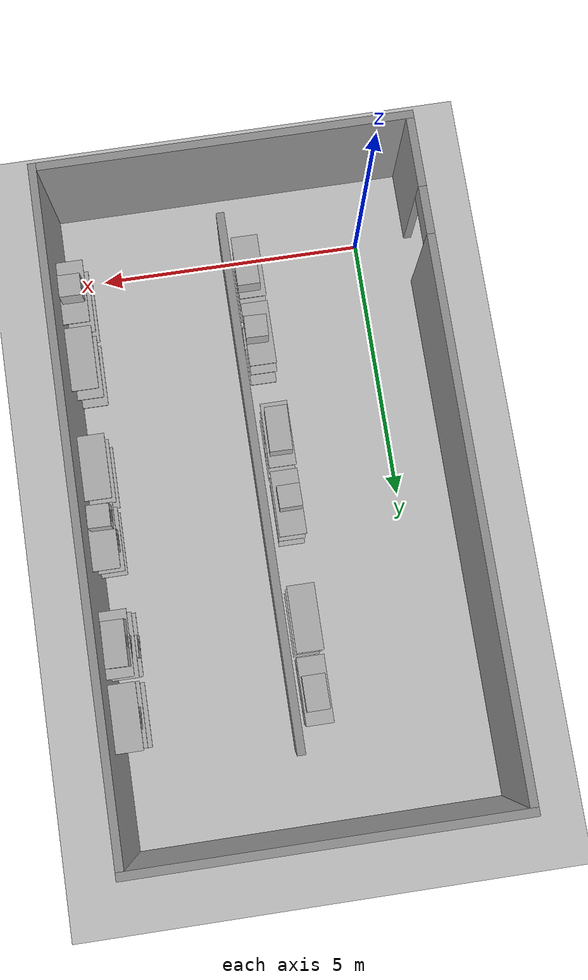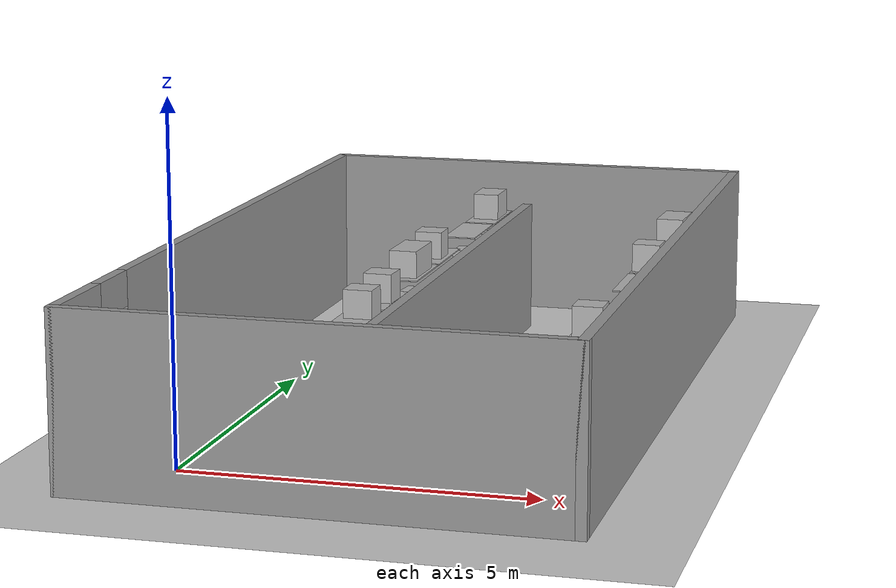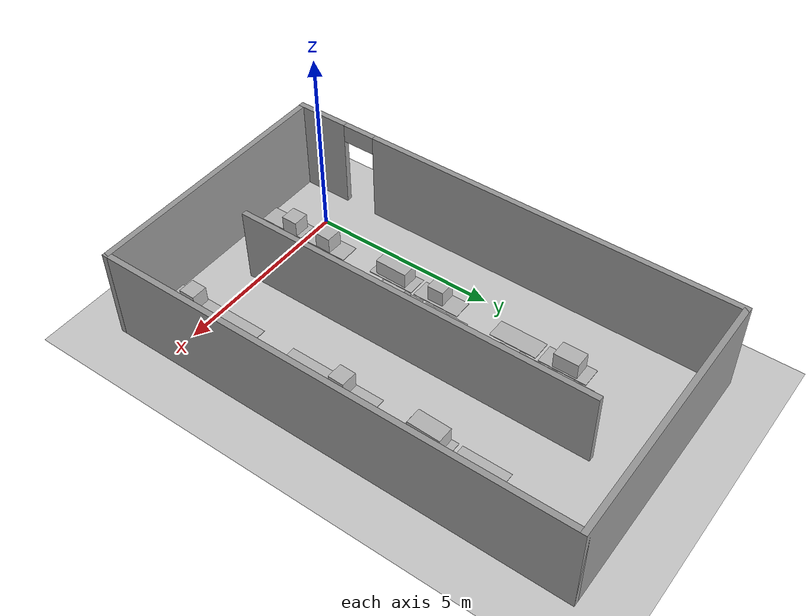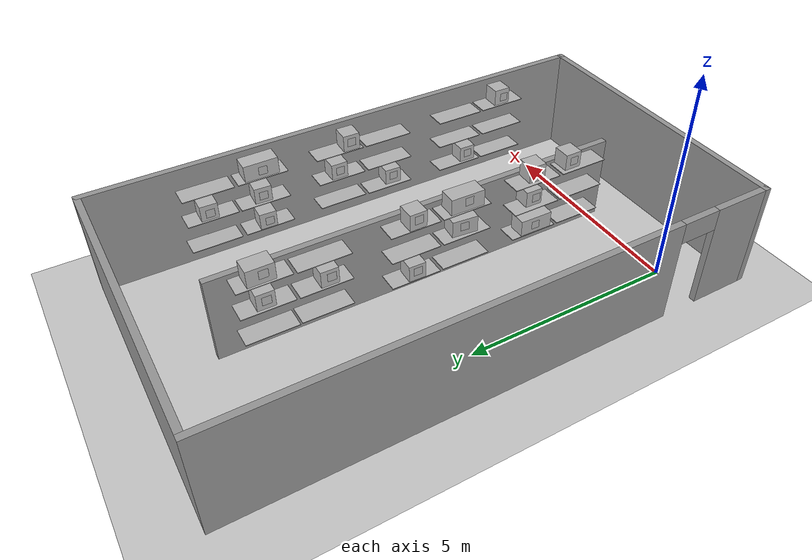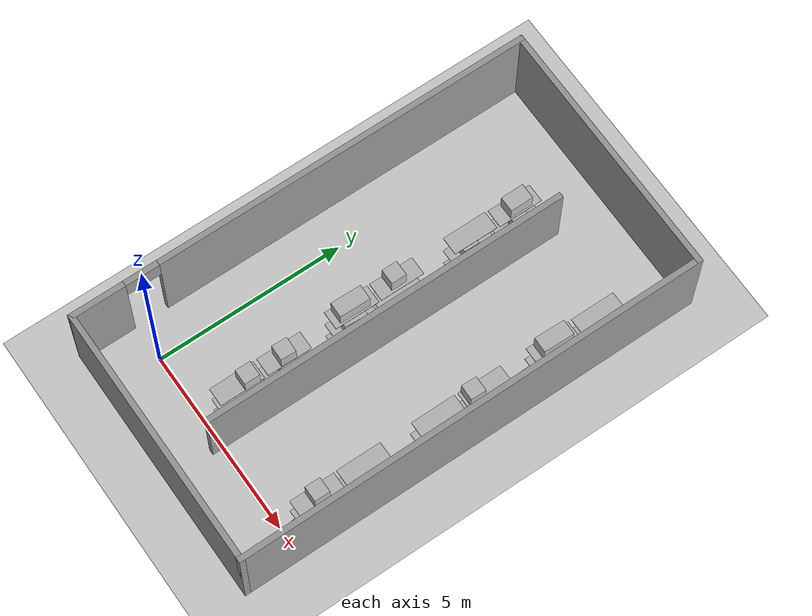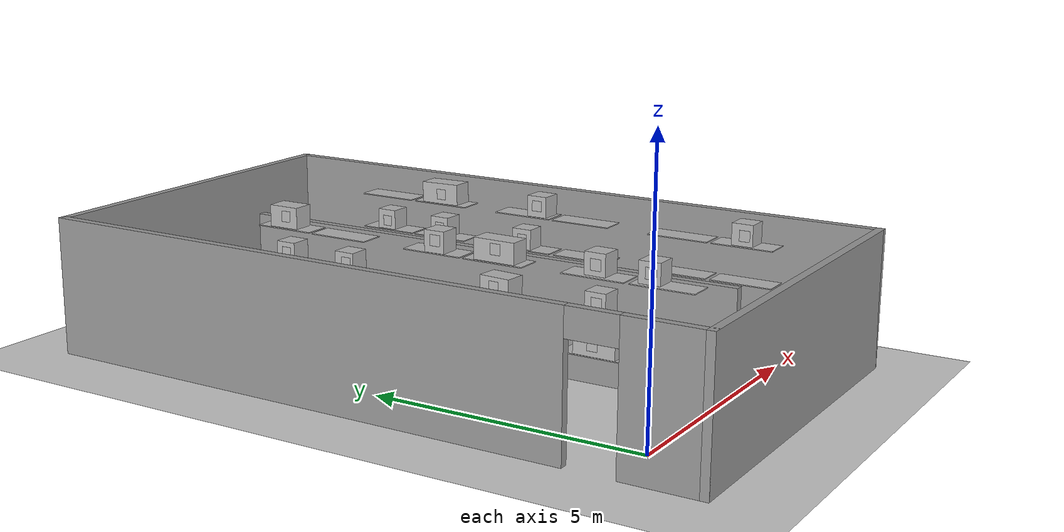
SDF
<sdf version="1.7">
 <world name="default">
  <plugin name="ros_interface_plugin" filename="librotors_gazebo_ros_interface_plugin.so"/>
  <light name="sun" type="directional">
   <pose>10 10 10 0 -0 0</pose>
   <diffuse>0.8 0.8 0.8 1</diffuse>
   <specular>0.2 0.2 0.2 1</specular>
   <attenuation>
    <range>1000</range>
    <constant>0.9</constant>
    <linear>0.01</linear>
    <quadratic>0.001</quadratic>
   </attenuation>
   <direction>-0.5 0.1 -0.9</direction>
   <spot><inner_angle>0</inner_angle><outer_angle>0</outer_angle><falloff>0</falloff></spot>
  </light>
  <model name="ground_plane">
   <static>1</static>
   <link name="link">
    <collision name="collision">
     <geometry><plane><normal>0 0 1</normal><size>300 300</size></plane></geometry>
     <surface>
      <contact><collide_bitmask>65535</collide_bitmask></contact>
      <friction><ode><mu>100</mu><mu2>50</mu2></ode></friction>
     </surface>
    </collision>
    <visual name="visual">
     <geometry><plane><normal>0 0 1</normal><size>100 100</size></plane></geometry>
     <material>
      <script><uri>file://media/materials/scripts/gazebo.material</uri><name>Gazebo/Grey</name></script>
     </material>
    </visual>
   </link>
  </model>
  <gravity>0 0 -9.8</gravity>
  <magnetic_field>6e-06 2.3e-05 -4.2e-05</magnetic_field>
  <atmosphere type="adiabatic"/>
  <physics name="default_physics" default="0" type="ode">
   <max_step_size>0.001</max_step_size>
   <real_time_factor>1</real_time_factor>
   <real_time_update_rate>1000</real_time_update_rate>
  </physics>
  <scene><ambient>0.4 0.4 0.4 1</ambient><background>0.7 0.7 0.7 1</background><shadows>1</shadows></scene>
  <spherical_coordinates>
   <surface_model>EARTH_WGS84</surface_model>
   <latitude_deg>0</latitude_deg>
   <longitude_deg>0</longitude_deg>
   <elevation>0</elevation>
   <heading_deg>0</heading_deg>
  </spherical_coordinates>
  <model name="unit_box">
   <link name="link">
    <inertial>
     <mass>0.00922354</mass>
     <inertia>
      <ixx>0.00104733</ixx>
      <ixy>0</ixy>
      <ixz>0</ixz>
      <iyy>0.000178965</iyy>
      <iyz>0</iyz>
      <izz>0.00122588</izz>
     </inertia>
    </inertial>
    <visual name="visual">
     <geometry><box><size>0.482252 1.16718 0.016436</size></box></geometry>
     <material>
      <script>
       <uri>model://unit_box/materials/scripts</uri>
       <uri>model://unit_box/materials/textures</uri>
       <name>shelveMat/Diffuse</name>
      </script>
      <shader type="pixel"/>
     </material>
    </visual>
    <collision name="collision"><geometry><box><size>0.482252 1.16718 0.016436</size></box></geometry></collision>
   </link>
   <static>1</static>
   <pose>2.18688 8.43309 2.00374 0 -1e-06 -0.002445</pose>
  </model>
  <model name="Caja">
   <link name="link">
    <pose>0 0 0.25 0 -0 0</pose>
    <inertial>
     <mass>0.39</mass>
     <inertia><ixx>0.00058</ixx><ixy>0</ixy><ixz>0</ixz><iyy>0.00058</iyy><iyz>0</iyz><izz>0.00019</izz></inertia>
    </inertial>
    <collision name="collision"><geometry><box><size>0.4 0.4 0.4</size></box></geometry></collision>
    <visual name="visual">
     <geometry><box><size>0.4 0.4 0.4</size></box></geometry>
     <material>
      <script>
       <uri>model://Caja/materials/scripts</uri>
       <uri>model://Caja/materials/textures</uri>
       <name>Caja/Diffuse</name>
      </script>
     </material>
    </visual>
   </link>
   <pose>2.26644 1.06331 1.95102 -7e-06 -1.2e-05 -0.001599</pose>
   <static>1</static>
  </model>
  <model name="CuboQR2">
   <link name="link">
    <pose>0 0 0.25 0 -0 0</pose>
    <inertial>
     <mass>0.39</mass>
     <inertia><ixx>0.00058</ixx><ixy>0</ixy><ixz>0</ixz><iyy>0.00058</iyy><iyz>0</iyz><izz>0.00019</izz></inertia>
    </inertial>
    <collision name="collision"><geometry><box><size>0.4 0.4 0.4</size></box></geometry></collision>
    <visual name="visual">
     <geometry><box><size>0.4 0.4 0.4</size></box></geometry>
     <material>
      <script>
       <uri>model://Caja/materials/scripts</uri>
       <uri>model://Caja/materials/textures</uri>
       <name>Caja/Diffuse</name>
      </script>
     </material>
    </visual>
   </link>
   <pose>2.25333 2.04265 1.96691 8e-06 4.1e-05 -0.030962</pose>
   <static>1</static>
  </model>
  <model name="CuboQR3">
   <link name="link">
    <pose>0 0 0.25 0 -0 0</pose>
    <inertial>
     <mass>0.39</mass>
     <inertia><ixx>0.00058</ixx><ixy>0</ixy><ixz>0</ixz><iyy>0.00058</iyy><iyz>0</iyz><izz>0.00019</izz></inertia>
    </inertial>
    <collision name="collision"><geometry><box><size>0.4 0.4 0.4</size></box></geometry></collision>
    <visual name="visual">
     <geometry><box><size>0.4 0.4 0.4</size></box></geometry>
     <material>
      <script>
       <uri>model://Caja/materials/scripts</uri>
       <uri>model://Caja/materials/textures</uri>
       <name>Caja/Diffuse</name>
      </script>
     </material>
    </visual>
   </link>
   <pose>2.29133 2.04465 1.28252 -1e-06 -8e-06 -0.026338</pose>
   <static>1</static>
  </model>
  <model name="CuboQR5">
   <link name="link">
    <pose>0 0 0.25 0 -0 0</pose>
    <inertial>
     <mass>0.39</mass>
     <inertia><ixx>0.00058</ixx><ixy>0</ixy><ixz>0</ixz><iyy>0.00058</iyy><iyz>0</iyz><izz>0.00019</izz></inertia>
    </inertial>
    <collision name="collision"><geometry><box><size>0.4 0.4 0.4</size></box></geometry></collision>
    <visual name="visual">
     <geometry><box><size>0.4 0.4 0.4</size></box></geometry>
     <material>
      <script>
       <uri>model://Caja/materials/scripts</uri>
       <uri>model://Caja/materials/textures</uri>
       <name>Caja/Diffuse</name>
      </script>
     </material>
    </visual>
   </link>
   <pose>2.20203 8.45266 1.29226 2.2e-05 -5.4e-05 -0.012577</pose>
   <static>1</static>
  </model>
  <model name="CuboQR6">
   <link name="link">
    <pose>0 0 0.25 0 -0 0</pose>
    <inertial>
     <mass>0.39</mass>
     <inertia><ixx>0.00058</ixx><ixy>0</ixy><ixz>0</ixz><iyy>0.00058</iyy><iyz>0</iyz><izz>0.00019</izz></inertia>
    </inertial>
    <collision name="collision"><geometry><box><size>0.4 0.4 0.4</size></box></geometry></collision>
    <visual name="visual">
     <geometry><box><size>0.4 0.4 0.4</size></box></geometry>
     <material>
      <script>
       <uri>model://Caja/materials/scripts</uri>
       <uri>model://Caja/materials/textures</uri>
       <name>Caja/Diffuse</name>
      </script>
     </material>
    </visual>
   </link>
   <pose>2.1851 7.10543 1.28642 2e-06 -1.1e-05 -0.010095</pose>
   <static>1</static>
  </model>
  <model name="CuboQR8">
   <link name="link">
    <pose>0 0 0.25 0 -0 0</pose>
    <inertial>
     <mass>0.39</mass>
     <inertia><ixx>0.00058</ixx><ixy>0</ixy><ixz>0</ixz><iyy>0.00058</iyy><iyz>0</iyz><izz>0.00019</izz></inertia>
    </inertial>
    <collision name="collision"><geometry><box><size>0.4 0.8 0.4</size></box></geometry></collision>
    <visual name="visual">
     <geometry><box><size>0.4 0.8 0.4</size></box></geometry>
     <material>
      <script>
       <uri>model://Caja/materials/scripts</uri>
       <uri>model://Caja/materials/textures</uri>
       <name>Caja/Diffuse</name>
      </script>
     </material>
    </visual>
   </link>
   <pose>2.14027 3.91275 1.94922 1.1e-05 -2e-06 -0.016923</pose>
   <static>1</static>
  </model>
  <model name="CuboQR9">
   <link name="link">
    <pose>0 0 0.25 0 -0 0</pose>
    <inertial>
     <mass>0.39</mass>
     <inertia><ixx>0.00058</ixx><ixy>0</ixy><ixz>0</ixz><iyy>0.00058</iyy><iyz>0</iyz><izz>0.00019</izz></inertia>
    </inertial>
    <collision name="collision"><geometry><box><size>0.4 0.4 0.4</size></box></geometry></collision>
    <visual name="visual">
     <geometry><box><size>0.4 0.4 0.4</size></box></geometry>
     <material>
      <script>
       <uri>model://Caja/materials/scripts</uri>
       <uri>model://Caja/materials/textures</uri>
       <name>Caja/Diffuse</name>
      </script>
     </material>
    </visual>
   </link>
   <pose>2.12545 5.14181 0.595564 -2.3e-05 -4e-06 -0.026435</pose>
   <static>1</static>
  </model>
  <model name="CuboQR10">
   <link name="link">
    <pose>0 0 0.25 0 -0 0</pose>
    <inertial>
     <mass>0.39</mass>
     <inertia><ixx>0.00058</ixx><ixy>0</ixy><ixz>0</ixz><iyy>0.00058</iyy><iyz>0</iyz><izz>0.00019</izz></inertia>
    </inertial>
    <collision name="collision"><geometry><box><size>0.4 0.4 0.4</size></box></geometry></collision>
    <visual name="visual">
     <geometry><box><size>0.4 0.4 0.4</size></box></geometry>
     <material>
      <script>
       <uri>model://Caja/materials/scripts</uri>
       <uri>model://Caja/materials/textures</uri>
       <name>Caja/Diffuse</name>
      </script>
     </material>
    </visual>
   </link>
   <pose>2.12667 5.11458 1.95849 1.8e-05 -7e-06 0.006396</pose>
   <static>1</static>
  </model>
  <model name="CuboQR12">
   <link name="link">
    <pose>0 0 0.25 0 -0 0</pose>
    <inertial>
     <mass>0.39</mass>
     <inertia><ixx>0.00058</ixx><ixy>0</ixy><ixz>0</ixz><iyy>0.00058</iyy><iyz>0</iyz><izz>0.00019</izz></inertia>
    </inertial>
    <collision name="collision"><geometry><box><size>0.4 0.4 0.4</size></box></geometry></collision>
    <visual name="visual">
     <geometry><box><size>0.4 0.4 0.4</size></box></geometry>
     <material>
      <script>
       <uri>model://Caja/materials/scripts</uri>
       <uri>model://Caja/materials/textures</uri>
       <name>Caja/Diffuse</name>
      </script>
     </material>
    </visual>
   </link>
   <pose>5.50959 3.87543 0.594128 2.2e-05 -1.4e-05 -0.039015</pose>
   <static>1</static>
  </model>
  <model name="CuboQR14">
   <link name="link">
    <pose>0 0 0.25 0 -0 0</pose>
    <inertial>
     <mass>0.39</mass>
     <inertia><ixx>0.00058</ixx><ixy>0</ixy><ixz>0</ixz><iyy>0.00058</iyy><iyz>0</iyz><izz>0.00019</izz></inertia>
    </inertial>
    <collision name="collision"><geometry><box><size>0.4 0.4 0.4</size></box></geometry></collision>
    <visual name="visual">
     <geometry><box><size>0.4 0.4 0.4</size></box></geometry>
     <material>
      <script>
       <uri>model://Caja/materials/scripts</uri>
       <uri>model://Caja/materials/textures</uri>
       <name>Caja/Diffuse</name>
      </script>
     </material>
    </visual>
   </link>
   <pose>5.45074 7.19681 1.28045 6.6e-05 -3e-06 -0.051107</pose>
   <static>1</static>
  </model>
  <model name="CuboQR15">
   <link name="link">
    <pose>0 0 0.25 0 -0 0</pose>
    <inertial>
     <mass>0.39</mass>
     <inertia><ixx>0.00058</ixx><ixy>0</ixy><ixz>0</ixz><iyy>0.00058</iyy><iyz>0</iyz><izz>0.00019</izz></inertia>
    </inertial>
    <collision name="collision"><geometry><box><size>0.4 0.4 0.4</size></box></geometry></collision>
    <visual name="visual">
     <geometry><box><size>0.4 0.4 0.4</size></box></geometry>
     <material>
      <script>
       <uri>model://Caja/materials/scripts</uri>
       <uri>model://Caja/materials/textures</uri>
       <name>Caja/Diffuse</name>
      </script>
     </material>
    </visual>
   </link>
   <pose>5.37041 7.19118 0.618783 1.4e-05 9e-06 -0.038014</pose>
   <static>1</static>
  </model>
  <model name="CuboQR17">
   <link name="link">
    <pose>0 0 0.25 0 -0 0</pose>
    <inertial>
     <mass>0.39</mass>
     <inertia><ixx>0.00058</ixx><ixy>0</ixy><ixz>0</ixz><iyy>0.00058</iyy><iyz>0</iyz><izz>0.00019</izz></inertia>
    </inertial>
    <collision name="collision"><geometry><box><size>0.4 0.4 0.4</size></box></geometry></collision>
    <visual name="visual">
     <geometry><box><size>0.4 0.4 0.4</size></box></geometry>
     <material>
      <script>
       <uri>model://Caja/materials/scripts</uri>
       <uri>model://Caja/materials/textures</uri>
       <name>Caja/Diffuse</name>
      </script>
     </material>
    </visual>
   </link>
   <pose>5.69081 8.45349 1.52593 1.5708 6e-06 -1.59061</pose>
   <static>1</static>
  </model>
  <model name="CuboQR19">
   <link name="link">
    <pose>0 0 0.25 0 -0 0</pose>
    <inertial>
     <mass>0.39</mass>
     <inertia><ixx>0.00058</ixx><ixy>0</ixy><ixz>0</ixz><iyy>0.00058</iyy><iyz>0</iyz><izz>0.00019</izz></inertia>
    </inertial>
    <collision name="collision"><geometry><box><size>0.4 0.4 0.4</size></box></geometry></collision>
    <visual name="visual">
     <geometry><box><size>0.4 0.4 0.4</size></box></geometry>
     <material>
      <script>
       <uri>model://Caja/materials/scripts</uri>
       <uri>model://Caja/materials/textures</uri>
       <name>Caja/Diffuse</name>
      </script>
     </material>
    </visual>
   </link>
   <pose>5.15759 0.816551 2.21624 -1.54376 1.57077 -1.55301</pose>
   <static>1</static>
  </model>
  <model name="CuboQR20">
   <link name="link">
    <pose>0 0 0.25 0 -0 0</pose>
    <inertial>
     <mass>0.39</mass>
     <inertia><ixx>0.00058</ixx><ixy>0</ixy><ixz>0</ixz><iyy>0.00058</iyy><iyz>0</iyz><izz>0.00019</izz></inertia>
    </inertial>
    <collision name="collision"><geometry><box><size>0.4 0.4 0.4</size></box></geometry></collision>
    <visual name="visual">
     <geometry><box><size>0.4 0.4 0.4</size></box></geometry>
     <material>
      <script>
       <uri>model://Caja/materials/scripts</uri>
       <uri>model://Caja/materials/textures</uri>
       <name>Caja/Diffuse</name>
      </script>
     </material>
    </visual>
   </link>
   <pose>5.18164 1.77873 0.844999 0.315724 1.57071 0.295641</pose>
   <static>1</static>
  </model>
  <model name="CuboQR27">
   <link name="link">
    <pose>0 0 0.25 0 -0 0</pose>
    <inertial>
     <mass>0.39</mass>
     <inertia><ixx>0.00058</ixx><ixy>0</ixy><ixz>0</ixz><iyy>0.00058</iyy><iyz>0</iyz><izz>0.00019</izz></inertia>
    </inertial>
    <collision name="collision"><geometry><box><size>0.4 0.4 0.4</size></box></geometry></collision>
    <visual name="visual">
     <geometry><box><size>0.4 0.4 0.4</size></box></geometry>
     <material>
      <script>
       <uri>model://Caja/materials/scripts</uri>
       <uri>model://Caja/materials/textures</uri>
       <name>Caja/Diffuse</name>
      </script>
     </material>
    </visual>
   </link>
   <pose>5.43264 5.31939 1.28624 1.3e-05 -2.3e-05 0.003723</pose>
   <static>1</static>
  </model>
  <model name="CuboQR29">
   <link name="link">
    <pose>0 0 0.25 0 -0 0</pose>
    <inertial>
     <mass>0.39</mass>
     <inertia><ixx>0.00058</ixx><ixy>0</ixy><ixz>0</ixz><iyy>0.00058</iyy><iyz>0</iyz><izz>0.00019</izz></inertia>
    </inertial>
    <collision name="collision"><geometry><box><size>0.4 0.4 0.4</size></box></geometry></collision>
    <visual name="visual">
     <geometry><box><size>0.4 0.4 0.4</size></box></geometry>
     <material>
      <script>
       <uri>model://Caja/materials/scripts</uri>
       <uri>model://Caja/materials/textures</uri>
       <name>Caja/Diffuse</name>
      </script>
     </material>
    </visual>
   </link>
   <pose>5.41781 4.97441 1.96483 1.6e-05 -1e-05 -0.024073</pose>
   <static>1</static>
  </model>
  <model name="CuboQR30">
   <link name="link">
    <pose>0 0 0.25 0 -0 0</pose>
    <inertial>
     <mass>0.39</mass>
     <inertia><ixx>0.00058</ixx><ixy>0</ixy><ixz>0</ixz><iyy>0.00058</iyy><iyz>0</iyz><izz>0.00019</izz></inertia>
    </inertial>
    <collision name="collision"><geometry><box><size>0.4 0.6 0.4</size></box></geometry></collision>
    <visual name="visual">
     <geometry><box><size>0.4 0.6 0.4</size></box></geometry>
     <material>
      <script>
       <uri>model://Caja/materials/scripts</uri>
       <uri>model://Caja/materials/textures</uri>
       <name>Caja/Diffuse</name>
      </script>
     </material>
    </visual>
   </link>
   <pose>2.19014 3.91484 1.28838 1e-05 -7e-06 -0.095429</pose>
   <static>1</static>
  </model>
  <model name="CuboQR32">
   <link name="link">
    <pose>0 0 0.25 0 -0 0</pose>
    <inertial>
     <mass>0.39</mass>
     <inertia><ixx>0.00058</ixx><ixy>0</ixy><ixz>0</ixz><iyy>0.00058</iyy><iyz>0</iyz><izz>0.00019</izz></inertia>
    </inertial>
    <collision name="collision"><geometry><box><size>0.4 0.6 0.4</size></box></geometry></collision>
    <visual name="visual">
     <geometry><box><size>0.4 0.6 0.4</size></box></geometry>
     <material>
      <script>
       <uri>model://Caja/materials/scripts</uri>
       <uri>model://Caja/materials/textures</uri>
       <name>Caja/Diffuse</name>
      </script>
     </material>
    </visual>
   </link>
   <pose>2.19132 8.47328 1.96092 5e-06 -8e-06 0.005056</pose>
   <static>1</static>
  </model>
  <model name="Estanterias2">
   <link name="Wall_7">
    <pose>-9.54199 -5.19373 -0.244468 0 -0 1.5708</pose>
    <inertial>
     <inertia><ixx>0</ixx><ixy>0</ixy><ixz>0</ixz><iyy>0</iyy><iyz>0</iyz><izz>0</izz></inertia>
     <mass>0</mass>
    </inertial>
    <visual name="Wall_7_Visual">
     <pose>0 0 1.25 0 -0 0</pose>
     <geometry><box><size>9.74609 0.15 2.08966</size></box></geometry>
     <material>
      <script><uri>file://media/materials/scripts/gazebo.material</uri><name>Gazebo/Grey</name></script>
      <ambient>1 1 1 1</ambient>
      <shader type="pixel"/>
      <diffuse>0.7 0.7 0.7 1</diffuse>
      <specular>0.01 0.01 0.01 1</specular>
      <emissive>0 0 0 1</emissive>
     </material>
     <meta><layer>0</layer></meta>
    </visual>
    <collision name="Wall_7_Collision">
     <pose>0 0 1.25 0 -0 0</pose>
     <geometry><box><size>9.74609 0.15 2.08966</size></box></geometry>
    </collision>
   </link>
   <static>1</static>
   <pose>12.1235 9.79263 0 0 -0 0</pose>
  </model>
  <model name="qrware">
   <pose>2.36907 4.73911 0 0 -0 0</pose>
   <link name="Wall_2">
    <pose>-3.425 0 0 0 -0 1.5708</pose>
    <visual name="Wall_2_Visual_0">
     <pose>-5.51907 0 1.25 0 -0 0</pose>
     <geometry><box><size>1.46186 0.15 2.5</size></box></geometry>
     <material>
      <script><uri>file://media/materials/scripts/gazebo.material</uri><name>Gazebo/Grey</name></script>
      <ambient>1 1 1 1</ambient>
     </material>
     <meta><layer>0</layer></meta>
    </visual>
    <collision name="Wall_2_Collision_0">
     <geometry><box><size>1.46186 0.15 2.5</size></box></geometry>
     <pose>-5.51907 0 1.25 0 -0 0</pose>
    </collision>
    <visual name="Wall_2_Visual_1">
     <pose>1.18093 0 1.25 0 -0 0</pose>
     <geometry><box><size>10.1381 0.15 2.5</size></box></geometry>
     <material>
      <script><uri>file://media/materials/scripts/gazebo.material</uri><name>Gazebo/Grey</name></script>
      <ambient>1 1 1 1</ambient>
     </material>
     <meta><layer>0</layer></meta>
    </visual>
    <collision name="Wall_2_Collision_1">
     <geometry><box><size>10.1381 0.15 2.5</size></box></geometry>
     <pose>1.18093 0 1.25 0 -0 0</pose>
    </collision>
    <visual name="Wall_2_Visual_2">
     <pose>-4.33814 0 2.25 0 -0 0</pose>
     <geometry><box><size>0.9 0.15 0.5</size></box></geometry>
     <material>
      <script><uri>file://media/materials/scripts/gazebo.material</uri><name>Gazebo/Grey</name></script>
      <ambient>1 1 1 1</ambient>
     </material>
     <meta><layer>0</layer></meta>
    </visual>
    <collision name="Wall_2_Collision_2">
     <geometry><box><size>0.9 0.15 0.5</size></box></geometry>
     <pose>-4.33814 0 2.25 0 -0 0</pose>
    </collision>
   </link>
   <link name="Wall_3">
    <collision name="Wall_3_Collision">
     <geometry><box><size>7 0.15 2.5</size></box></geometry>
     <pose>0 0 1.25 0 -0 0</pose>
    </collision>
    <visual name="Wall_3_Visual">
     <pose>0 0 1.25 0 -0 0</pose>
     <geometry><box><size>7 0.15 2.5</size></box></geometry>
     <material>
      <script><uri>file://media/materials/scripts/gazebo.material</uri><name>Gazebo/Grey</name></script>
      <ambient>1 1 1 1</ambient>
     </material>
     <meta><layer>0</layer></meta>
    </visual>
    <pose>0 6.175 0 0 -0 0</pose>
   </link>
   <link name="Wall_4">
    <collision name="Wall_4_Collision">
     <geometry><box><size>12.5 0.15 2.5</size></box></geometry>
     <pose>0 0 1.25 0 -0 0</pose>
    </collision>
    <visual name="Wall_4_Visual">
     <pose>0 0 1.25 0 -0 0</pose>
     <geometry><box><size>12.5 0.15 2.5</size></box></geometry>
     <material>
      <script><uri>file://media/materials/scripts/gazebo.material</uri><name>Gazebo/Grey</name></script>
      <ambient>1 1 1 1</ambient>
     </material>
     <meta><layer>0</layer></meta>
    </visual>
    <pose>3.425 0 0 0 0 -1.5708</pose>
   </link>
   <link name="Wall_6">
    <collision name="Wall_6_Collision">
     <geometry><box><size>7 0.15 2.5</size></box></geometry>
     <pose>0 0 1.25 0 -0 0</pose>
    </collision>
    <visual name="Wall_6_Visual">
     <pose>0 0 1.25 0 -0 0</pose>
     <geometry><box><size>7 0.15 2.5</size></box></geometry>
     <material>
      <script><uri>file://media/materials/scripts/gazebo.material</uri><name>Gazebo/Grey</name></script>
      <ambient>1 1 1 1</ambient>
     </material>
     <meta><layer>0</layer></meta>
    </visual>
    <pose>0 -6.175 0 0 -0 0</pose>
   </link>
   <static>1</static>
  </model>
  <audio><device>default</device></audio>
  <model name="CuboQR8_clone">
   <link name="link">
    <pose>0 0 0.25 0 -0 0</pose>
    <inertial>
     <mass>0.39</mass>
     <inertia><ixx>0.00058</ixx><ixy>0</ixy><ixz>0</ixz><iyy>0.00058</iyy><iyz>0</iyz><izz>0.00019</izz></inertia>
    </inertial>
    <collision name="collision"><geometry><box><size>0.4 0.8 0.4</size></box></geometry></collision>
    <visual name="visual">
     <geometry><box><size>0.4 0.8 0.4</size></box></geometry>
     <material>
      <script>
       <uri>model://Caja/materials/scripts</uri>
       <uri>model://Caja/materials/textures</uri>
       <name>Caja/Diffuse</name>
      </script>
     </material>
    </visual>
   </link>
   <pose>5.42477 7.16275 1.96227 -0.019933 -7e-06 -0.017982</pose>
   <static>1</static>
  </model>
  <model name="Plano4_0">
   <link name="link">
    <gravity>0</gravity>
    <pose>0 0 0.25 0 -0 0</pose>
    <inertial>
     <mass>1e-06</mass>
     <inertia><ixx>0.00058</ixx><ixy>0</ixy><ixz>0</ixz><iyy>0.00058</iyy><iyz>0</iyz><izz>0.00019</izz></inertia>
    </inertial>
    <collision name="collision"><geometry><box><size>0.2 1e-06 0.2</size></box></geometry></collision>
    <visual name="visual">
     <geometry><box><size>0.2 1e-06 0.2</size></box></geometry>
     <material>
      <script>
       <uri>model://Plano4/materials/scripts</uri>
       <uri>model://Plano4/materials/textures</uri>
       <name>Plano4/Diffuse</name>
      </script>
     </material>
    </visual>
   </link>
   <pose>1.978 2.02492 0.597619 0 0 -1.59006</pose>
  </model>
  <model name="Plano9">
   <link name="link">
    <gravity>0</gravity>
    <pose>0 0 0.25 0 -0 0</pose>
    <inertial>
     <mass>1e-06</mass>
     <inertia><ixx>0.00058</ixx><ixy>0</ixy><ixz>0</ixz><iyy>0.00058</iyy><iyz>0</iyz><izz>0.00019</izz></inertia>
    </inertial>
    <collision name="collision"><geometry><box><size>0.2 1e-06 0.2</size></box></geometry></collision>
    <visual name="visual">
     <geometry><box><size>0.2 1e-06 0.2</size></box></geometry>
     <material>
      <script>
       <uri>model://Plano9/materials/scripts</uri>
       <uri>model://Plano9/materials/textures</uri>
       <name>Plano9/Diffuse</name>
      </script>
     </material>
    </visual>
   </link>
   <pose>1.92313 5.13661 0.621101 0 0 -1.58642</pose>
  </model>
  <model name="CuboQR8_clone_0">
   <link name="link">
    <pose>0 0 0.25 0 -0 0</pose>
    <inertial>
     <mass>0.39</mass>
     <inertia><ixx>0.00058</ixx><ixy>0</ixy><ixz>0</ixz><iyy>0.00058</iyy><iyz>0</iyz><izz>0.00019</izz></inertia>
    </inertial>
    <collision name="collision"><geometry><box><size>0.4 0.8 0.4</size></box></geometry></collision>
    <visual name="visual">
     <geometry><box><size>0.4 0.8 0.4</size></box></geometry>
     <material>
      <script>
       <uri>model://Caja/materials/scripts</uri>
       <uri>model://Caja/materials/textures</uri>
       <name>Caja/Diffuse</name>
      </script>
     </material>
    </visual>
   </link>
   <pose>2.18311 1.99541 0.596214 -1e-05 1e-06 -0.016913</pose>
   <static>1</static>
  </model>
  <model name="Plano5">
   <link name="link">
    <gravity>0</gravity>
    <pose>0 0 0.25 0 -0 0</pose>
    <inertial>
     <mass>1e-06</mass>
     <inertia><ixx>0.00058</ixx><ixy>0</ixy><ixz>0</ixz><iyy>0.00058</iyy><iyz>0</iyz><izz>0.00019</izz></inertia>
    </inertial>
    <collision name="collision"><geometry><box><size>0.2 1e-06 0.2</size></box></geometry></collision>
    <visual name="visual">
     <geometry><box><size>0.2 1e-06 0.2</size></box></geometry>
     <material>
      <script>
       <uri>model://Plano5/materials/scripts</uri>
       <uri>model://Plano5/materials/textures</uri>
       <name>Plano5/Diffuse</name>
      </script>
     </material>
    </visual>
   </link>
   <pose>2.00061 8.43579 1.29742 0 0 -1.58596</pose>
  </model>
  <model name="Plano6">
   <link name="link">
    <gravity>0</gravity>
    <pose>0 0 0.25 0 -0 0</pose>
    <inertial>
     <mass>1e-06</mass>
     <inertia><ixx>0.00058</ixx><ixy>0</ixy><ixz>0</ixz><iyy>0.00058</iyy><iyz>0</iyz><izz>0.00019</izz></inertia>
    </inertial>
    <collision name="collision"><geometry><box><size>0.2 1e-06 0.2</size></box></geometry></collision>
    <visual name="visual">
     <geometry><box><size>0.2 1e-06 0.2</size></box></geometry>
     <material>
      <script>
       <uri>model://Plano6/materials/scripts</uri>
       <uri>model://Plano6/materials/textures</uri>
       <name>Plano6/Diffuse</name>
      </script>
     </material>
    </visual>
   </link>
   <pose>1.9843 7.06559 1.29818 0 0 -1.58047</pose>
  </model>
  <model name="Plano30">
   <link name="link">
    <gravity>0</gravity>
    <pose>0 0 0.25 0 -0 0</pose>
    <inertial>
     <mass>1e-06</mass>
     <inertia><ixx>0.00058</ixx><ixy>0</ixy><ixz>0</ixz><iyy>0.00058</iyy><iyz>0</iyz><izz>0.00019</izz></inertia>
    </inertial>
    <collision name="collision"><geometry><box><size>0.2 1e-06 0.2</size></box></geometry></collision>
    <visual name="visual">
     <geometry><box><size>0.2 1e-06 0.2</size></box></geometry>
     <material>
      <script>
       <uri>model://Plano30/materials/scripts</uri>
       <uri>model://Plano30/materials/textures</uri>
       <name>Plano30/Diffuse</name>
      </script>
     </material>
    </visual>
   </link>
   <pose>1.9915 3.94414 1.31063 0 0 -1.66883</pose>
  </model>
  <model name="Plano3">
   <link name="link">
    <gravity>0</gravity>
    <pose>0 0 0.25 0 -0 0</pose>
    <inertial>
     <mass>1e-06</mass>
     <inertia><ixx>0.00058</ixx><ixy>0</ixy><ixz>0</ixz><iyy>0.00058</iyy><iyz>0</iyz><izz>0.00019</izz></inertia>
    </inertial>
    <collision name="collision"><geometry><box><size>0.2 1e-06 0.2</size></box></geometry></collision>
    <visual name="visual">
     <geometry><box><size>0.2 1e-06 0.2</size></box></geometry>
     <material>
      <script>
       <uri>model://Plano3/materials/scripts</uri>
       <uri>model://Plano3/materials/textures</uri>
       <name>Plano3/Diffuse</name>
      </script>
     </material>
    </visual>
   </link>
   <pose>2.06585 2.0112 1.29904 0 0 -1.60488</pose>
  </model>
  <model name="Plano2">
   <link name="link">
    <gravity>0</gravity>
    <pose>0 0 0.25 0 -0 0</pose>
    <inertial>
     <mass>1e-06</mass>
     <inertia><ixx>0.00058</ixx><ixy>0</ixy><ixz>0</ixz><iyy>0.00058</iyy><iyz>0</iyz><izz>0.00019</izz></inertia>
    </inertial>
    <collision name="collision"><geometry><box><size>0.2 1e-06 0.2</size></box></geometry></collision>
    <visual name="visual">
     <geometry><box><size>0.2 1e-06 0.2</size></box></geometry>
     <material>
      <script>
       <uri>model://Plano2/materials/scripts</uri>
       <uri>model://Plano2/materials/textures</uri>
       <name>Plano2/Diffuse</name>
      </script>
     </material>
    </visual>
   </link>
   <pose>2.05247 2.02975 1.96021 0 0 -1.6005</pose>
  </model>
  <model name="Plano">
   <link name="link">
    <gravity>0</gravity>
    <pose>0 0 0.25 0 -0 0</pose>
    <inertial>
     <mass>1e-06</mass>
     <inertia><ixx>0.00058</ixx><ixy>0</ixy><ixz>0</ixz><iyy>0.00058</iyy><iyz>0</iyz><izz>0.00019</izz></inertia>
    </inertial>
    <collision name="collision"><geometry><box><size>0.2 1e-06 0.2</size></box></geometry></collision>
    <visual name="visual">
     <geometry><box><size>0.2 1e-06 0.2</size></box></geometry>
     <material>
      <script>
       <uri>model://Plano/materials/scripts</uri>
       <uri>model://Plano/materials/textures</uri>
       <name>Plano/Diffuse</name>
      </script>
     </material>
    </visual>
   </link>
   <pose>2.06285 1.03786 1.95496 0 0 -1.57561</pose>
  </model>
  <model name="Plano8">
   <link name="link">
    <gravity>0</gravity>
    <pose>0 0 0.25 0 -0 0</pose>
    <inertial>
     <mass>1e-06</mass>
     <inertia><ixx>0.00058</ixx><ixy>0</ixy><ixz>0</ixz><iyy>0.00058</iyy><iyz>0</iyz><izz>0.00019</izz></inertia>
    </inertial>
    <collision name="collision"><geometry><box><size>0.2 1e-06 0.2</size></box></geometry></collision>
    <visual name="visual">
     <geometry><box><size>0.2 1e-06 0.2</size></box></geometry>
     <material>
      <script>
       <uri>model://Plano8/materials/scripts</uri>
       <uri>model://Plano8/materials/textures</uri>
       <name>Plano8/Diffuse</name>
      </script>
     </material>
    </visual>
   </link>
   <pose>1.93511 3.88666 1.99089 0 0 -1.57894</pose>
  </model>
  <model name="Plano10">
   <link name="link">
    <gravity>0</gravity>
    <pose>0 0 0.25 0 -0 0</pose>
    <inertial>
     <mass>1e-06</mass>
     <inertia><ixx>0.00058</ixx><ixy>0</ixy><ixz>0</ixz><iyy>0.00058</iyy><iyz>0</iyz><izz>0.00019</izz></inertia>
    </inertial>
    <collision name="collision"><geometry><box><size>0.2 1e-06 0.2</size></box></geometry></collision>
    <visual name="visual">
     <geometry><box><size>0.2 1e-06 0.2</size></box></geometry>
     <material>
      <script>
       <uri>model://Plano10/materials/scripts</uri>
       <uri>model://Plano10/materials/textures</uri>
       <name>Plano10/Diffuse</name>
      </script>
     </material>
    </visual>
   </link>
   <pose>1.92521 5.09842 1.98483 0 0 -1.55773</pose>
  </model>
  <model name="Plano32">
   <link name="link">
    <gravity>0</gravity>
    <pose>0 0 0.25 0 -0 0</pose>
    <inertial>
     <mass>1e-06</mass>
     <inertia><ixx>0.00058</ixx><ixy>0</ixy><ixz>0</ixz><iyy>0.00058</iyy><iyz>0</iyz><izz>0.00019</izz></inertia>
    </inertial>
    <collision name="collision"><geometry><box><size>0.2 1e-06 0.2</size></box></geometry></collision>
    <visual name="visual">
     <geometry><box><size>0.2 1e-06 0.2</size></box></geometry>
     <material>
      <script>
       <uri>model://Plano32/materials/scripts</uri>
       <uri>model://Plano32/materials/textures</uri>
       <name>Plano32/Diffuse</name>
      </script>
     </material>
    </visual>
   </link>
   <pose>1.98912 8.41841 1.97803 0 0 -1.58529</pose>
  </model>
  <model name="Plano29">
   <link name="link">
    <gravity>0</gravity>
    <pose>0 0 0.25 0 -0 0</pose>
    <inertial>
     <mass>1e-06</mass>
     <inertia><ixx>0.00058</ixx><ixy>0</ixy><ixz>0</ixz><iyy>0.00058</iyy><iyz>0</iyz><izz>0.00019</izz></inertia>
    </inertial>
    <collision name="collision"><geometry><box><size>0.2 1e-06 0.2</size></box></geometry></collision>
    <visual name="visual">
     <geometry><box><size>0.2 1e-06 0.2</size></box></geometry>
     <material>
      <script>
       <uri>model://Plano29/materials/scripts</uri>
       <uri>model://Plano29/materials/textures</uri>
       <name>Plano29/Diffuse</name>
      </script>
     </material>
    </visual>
   </link>
   <pose>5.2214 7.14046 1.94589 0 0 -1.5937</pose>
  </model>
  <model name="Plano26">
   <link name="link">
    <gravity>0</gravity>
    <pose>0 0 0.25 0 -0 0</pose>
    <inertial>
     <mass>1e-06</mass>
     <inertia><ixx>0.00058</ixx><ixy>0</ixy><ixz>0</ixz><iyy>0.00058</iyy><iyz>0</iyz><izz>0.00019</izz></inertia>
    </inertial>
    <collision name="collision"><geometry><box><size>0.2 1e-06 0.2</size></box></geometry></collision>
    <visual name="visual">
     <geometry><box><size>0.2 1e-06 0.2</size></box></geometry>
     <material>
      <script>
       <uri>model://Plano26/materials/scripts</uri>
       <uri>model://Plano26/materials/textures</uri>
       <name>Plano26/Diffuse</name>
      </script>
     </material>
    </visual>
   </link>
   <pose>5.21638 4.97769 1.97723 0 0 -1.59341</pose>
  </model>
  <model name="Plano27">
   <link name="link">
    <gravity>0</gravity>
    <pose>0 0 0.25 0 -0 0</pose>
    <inertial>
     <mass>1e-06</mass>
     <inertia><ixx>0.00058</ixx><ixy>0</ixy><ixz>0</ixz><iyy>0.00058</iyy><iyz>0</iyz><izz>0.00019</izz></inertia>
    </inertial>
    <collision name="collision"><geometry><box><size>0.2 1e-06 0.2</size></box></geometry></collision>
    <visual name="visual">
     <geometry><box><size>0.2 1e-06 0.2</size></box></geometry>
     <material>
      <script>
       <uri>model://Plano27/materials/scripts</uri>
       <uri>model://Plano27/materials/textures</uri>
       <name>Plano27/Diffuse</name>
      </script>
     </material>
    </visual>
   </link>
   <pose>5.20009 0.767776 1.95296 0 0 -1.5745</pose>
  </model>
  <model name="Plano14">
   <link name="link">
    <gravity>0</gravity>
    <pose>0 0 0.25 0 -0 0</pose>
    <inertial>
     <mass>1e-06</mass>
     <inertia><ixx>0.00058</ixx><ixy>0</ixy><ixz>0</ixz><iyy>0.00058</iyy><iyz>0</iyz><izz>0.00019</izz></inertia>
    </inertial>
    <collision name="collision"><geometry><box><size>0.2 1e-06 0.2</size></box></geometry></collision>
    <visual name="visual">
     <geometry><box><size>0.2 1e-06 0.2</size></box></geometry>
     <material>
      <script>
       <uri>model://Plano14/materials/scripts</uri>
       <uri>model://Plano14/materials/textures</uri>
       <name>Plano14/Diffuse</name>
      </script>
     </material>
    </visual>
   </link>
   <pose>5.23242 5.3041 1.28653 0 0 -1.56728</pose>
  </model>
  <model name="Plano17">
   <link name="link">
    <gravity>0</gravity>
    <pose>0 0 0.25 0 -0 0</pose>
    <inertial>
     <mass>1e-06</mass>
     <inertia><ixx>0.00058</ixx><ixy>0</ixy><ixz>0</ixz><iyy>0.00058</iyy><iyz>0</iyz><izz>0.00019</izz></inertia>
    </inertial>
    <collision name="collision"><geometry><box><size>0.2 1e-06 0.2</size></box></geometry></collision>
    <visual name="visual">
     <geometry><box><size>0.2 1e-06 0.2</size></box></geometry>
     <material>
      <script>
       <uri>model://Plano17/materials/scripts</uri>
       <uri>model://Plano17/materials/textures</uri>
       <name>Plano17/Diffuse</name>
      </script>
     </material>
    </visual>
   </link>
   <pose>5.24803 7.19832 1.27237 0 0 -1.61196</pose>
  </model>
  <model name="Plano15">
   <link name="link">
    <gravity>0</gravity>
    <pose>0 0 0.25 0 -0 0</pose>
    <inertial>
     <mass>1e-06</mass>
     <inertia><ixx>0.00058</ixx><ixy>0</ixy><ixz>0</ixz><iyy>0.00058</iyy><iyz>0</iyz><izz>0.00019</izz></inertia>
    </inertial>
    <collision name="collision"><geometry><box><size>0.2 1e-06 0.2</size></box></geometry></collision>
    <visual name="visual">
     <geometry><box><size>0.2 1e-06 0.2</size></box></geometry>
     <material>
      <script>
       <uri>model://Plano15/materials/scripts</uri>
       <uri>model://Plano15/materials/textures</uri>
       <name>Plano15/Diffuse</name>
      </script>
     </material>
    </visual>
   </link>
   <pose>5.23972 8.44411 1.25459 0 0 -1.59575</pose>
  </model>
  <model name="Plano12">
   <link name="link">
    <gravity>0</gravity>
    <pose>0 0 0.25 0 -0 0</pose>
    <inertial>
     <mass>1e-06</mass>
     <inertia><ixx>0.00058</ixx><ixy>0</ixy><ixz>0</ixz><iyy>0.00058</iyy><iyz>0</iyz><izz>0.00019</izz></inertia>
    </inertial>
    <collision name="collision"><geometry><box><size>0.2 1e-06 0.2</size></box></geometry></collision>
    <visual name="visual">
     <geometry><box><size>0.2 1e-06 0.2</size></box></geometry>
     <material>
      <script>
       <uri>model://Plano12/materials/scripts</uri>
       <uri>model://Plano12/materials/textures</uri>
       <name>Plano12/Diffuse</name>
      </script>
     </material>
    </visual>
   </link>
   <pose>5.16376 7.16788 0.598453 0 0 -1.61005</pose>
  </model>
  <model name="Plano20">
   <link name="link">
    <gravity>0</gravity>
    <pose>0 0 0.25 0 -0 0</pose>
    <inertial>
     <mass>1e-06</mass>
     <inertia><ixx>0.00058</ixx><ixy>0</ixy><ixz>0</ixz><iyy>0.00058</iyy><iyz>0</iyz><izz>0.00019</izz></inertia>
    </inertial>
    <collision name="collision"><geometry><box><size>0.2 1e-06 0.2</size></box></geometry></collision>
    <visual name="visual">
     <geometry><box><size>0.2 1e-06 0.2</size></box></geometry>
     <material>
      <script>
       <uri>model://Plano20/materials/scripts</uri>
       <uri>model://Plano20/materials/textures</uri>
       <name>Plano20/Diffuse</name>
      </script>
     </material>
    </visual>
   </link>
   <pose>5.30498 3.87007 0.611968 0 0 -1.61273</pose>
  </model>
  <model name="unit_box_clone">
   <link name="link">
    <inertial>
     <mass>0.00922354</mass>
     <inertia>
      <ixx>0.00104733</ixx>
      <ixy>0</ixy>
      <ixz>0</ixz>
      <iyy>0.000178965</iyy>
      <iyz>0</iyz>
      <izz>0.00122588</izz>
     </inertia>
    </inertial>
    <visual name="visual">
     <geometry><box><size>0.482252 1.16718 0.016436</size></box></geometry>
     <material>
      <script>
       <uri>model://unit_box/materials/scripts</uri>
       <uri>model://unit_box/materials/textures</uri>
       <name>shelveMat/Diffuse</name>
      </script>
      <shader type="pixel"/>
     </material>
    </visual>
    <collision name="collision"><geometry><box><size>0.482252 1.16718 0.016436</size></box></geometry></collision>
   </link>
   <static>1</static>
   <pose>2.16612 7.19524 2.00375 0 -1e-06 -0.002445</pose>
  </model>
  <model name="unit_box_clone_clone">
   <link name="link">
    <inertial>
     <mass>0.00922354</mass>
     <inertia>
      <ixx>0.00104733</ixx>
      <ixy>0</ixy>
      <ixz>0</ixz>
      <iyy>0.000178965</iyy>
      <iyz>0</iyz>
      <izz>0.00122588</izz>
     </inertia>
    </inertial>
    <visual name="visual">
     <geometry><box><size>0.482252 1.16718 0.016436</size></box></geometry>
     <material>
      <script>
       <uri>model://unit_box/materials/scripts</uri>
       <uri>model://unit_box/materials/textures</uri>
       <name>shelveMat/Diffuse</name>
      </script>
      <shader type="pixel"/>
     </material>
    </visual>
    <collision name="collision"><geometry><box><size>0.482252 1.16718 0.016436</size></box></geometry></collision>
   </link>
   <static>1</static>
   <pose>2.15094 5.16802 2.00375 0 -1e-06 -0.002445</pose>
  </model>
  <model name="unit_box_clone_clone_clone">
   <link name="link">
    <inertial>
     <mass>0.00922354</mass>
     <inertia>
      <ixx>0.00104733</ixx>
      <ixy>0</ixy>
      <ixz>0</ixz>
      <iyy>0.000178965</iyy>
      <iyz>0</iyz>
      <izz>0.00122588</izz>
     </inertia>
    </inertial>
    <visual name="visual">
     <geometry><box><size>0.482252 1.16718 0.016436</size></box></geometry>
     <material>
      <script>
       <uri>model://unit_box/materials/scripts</uri>
       <uri>model://unit_box/materials/textures</uri>
       <name>shelveMat/Diffuse</name>
      </script>
      <shader type="pixel"/>
     </material>
    </visual>
    <collision name="collision"><geometry><box><size>0.482252 1.16718 0.016436</size></box></geometry></collision>
   </link>
   <static>1</static>
   <pose>2.14649 3.9345 2.00375 0 -1e-06 -0.002445</pose>
  </model>
  <model name="unit_box_clone_clone_clone_clone">
   <link name="link">
    <inertial>
     <mass>0.00922354</mass>
     <inertia>
      <ixx>0.00104733</ixx>
      <ixy>0</ixy>
      <ixz>0</ixz>
      <iyy>0.000178965</iyy>
      <iyz>0</iyz>
      <izz>0.00122588</izz>
     </inertia>
    </inertial>
    <visual name="visual">
     <geometry><box><size>0.482252 1.16718 0.016436</size></box></geometry>
     <material>
      <script>
       <uri>model://unit_box/materials/scripts</uri>
       <uri>model://unit_box/materials/textures</uri>
       <name>shelveMat/Diffuse</name>
      </script>
      <shader type="pixel"/>
     </material>
    </visual>
    <collision name="collision"><geometry><box><size>0.482252 1.16718 0.016436</size></box></geometry></collision>
   </link>
   <static>1</static>
   <pose>2.21591 2.05831 2.00375 0 -1e-06 -0.002445</pose>
  </model>
  <model name="unit_box_clone_clone_clone_clone_0">
   <link name="link">
    <inertial>
     <mass>0.00922354</mass>
     <inertia>
      <ixx>0.00104733</ixx>
      <ixy>0</ixy>
      <ixz>0</ixz>
      <iyy>0.000178965</iyy>
      <iyz>0</iyz>
      <izz>0.00122588</izz>
     </inertia>
    </inertial>
    <visual name="visual">
     <geometry><box><size>0.482252 1.16718 0.016436</size></box></geometry>
     <material>
      <script>
       <uri>model://unit_box/materials/scripts</uri>
       <uri>model://unit_box/materials/textures</uri>
       <name>shelveMat/Diffuse</name>
      </script>
      <shader type="pixel"/>
     </material>
    </visual>
    <collision name="collision"><geometry><box><size>0.482252 1.16718 0.016436</size></box></geometry></collision>
   </link>
   <static>1</static>
   <pose>2.21542 0.798436 2.00375 0 -1e-06 -0.002445</pose>
  </model>
  <model name="unit_box_clone_clone_clone_clone_1">
   <link name="link">
    <inertial>
     <mass>0.00922354</mass>
     <inertia>
      <ixx>0.00104733</ixx>
      <ixy>0</ixy>
      <ixz>0</ixz>
      <iyy>0.000178965</iyy>
      <iyz>0</iyz>
      <izz>0.00122588</izz>
     </inertia>
    </inertial>
    <visual name="visual">
     <geometry><box><size>0.482252 1.16718 0.016436</size></box></geometry>
     <material>
      <script>
       <uri>model://unit_box/materials/scripts</uri>
       <uri>model://unit_box/materials/textures</uri>
       <name>shelveMat/Diffuse</name>
      </script>
      <shader type="pixel"/>
     </material>
    </visual>
    <collision name="collision"><geometry><box><size>0.482252 1.16718 0.016436</size></box></geometry></collision>
   </link>
   <static>1</static>
   <pose>2.1868 8.43502 1.33671 0 -1e-06 -0.002445</pose>
  </model>
  <model name="unit_box_clone_clone_clone_clone_1_clone">
   <link name="link">
    <inertial>
     <mass>0.00922354</mass>
     <inertia>
      <ixx>0.00104733</ixx>
      <ixy>0</ixy>
      <ixz>0</ixz>
      <iyy>0.000178965</iyy>
      <iyz>0</iyz>
      <izz>0.00122588</izz>
     </inertia>
    </inertial>
    <visual name="visual">
     <geometry><box><size>0.482252 1.16718 0.016436</size></box></geometry>
     <material>
      <script>
       <uri>model://unit_box/materials/scripts</uri>
       <uri>model://unit_box/materials/textures</uri>
       <name>shelveMat/Diffuse</name>
      </script>
      <shader type="pixel"/>
     </material>
    </visual>
    <collision name="collision"><geometry><box><size>0.482252 1.16718 0.016436</size></box></geometry></collision>
   </link>
   <static>1</static>
   <pose>2.18219 7.19631 1.33212 0 -1e-06 -0.002445</pose>
  </model>
  <model name="unit_box_clone_clone_clone_clone_1_clone_0">
   <link name="link">
    <inertial>
     <mass>0.00922354</mass>
     <inertia>
      <ixx>0.00104733</ixx>
      <ixy>0</ixy>
      <ixz>0</ixz>
      <iyy>0.000178965</iyy>
      <iyz>0</iyz>
      <izz>0.00122588</izz>
     </inertia>
    </inertial>
    <visual name="visual">
     <geometry><box><size>0.482252 1.16718 0.016436</size></box></geometry>
     <material>
      <script>
       <uri>model://unit_box/materials/scripts</uri>
       <uri>model://unit_box/materials/textures</uri>
       <name>shelveMat/Diffuse</name>
      </script>
      <shader type="pixel"/>
     </material>
    </visual>
    <collision name="collision"><geometry><box><size>0.482252 1.16718 0.016436</size></box></geometry></collision>
   </link>
   <static>1</static>
   <pose>2.15829 5.15878 1.33212 0 -1e-06 -0.002445</pose>
  </model>
  <model name="unit_box_clone_clone_clone_clone_1_clone_1">
   <link name="link">
    <inertial>
     <mass>0.00922354</mass>
     <inertia>
      <ixx>0.00104733</ixx>
      <ixy>0</ixy>
      <ixz>0</ixz>
      <iyy>0.000178965</iyy>
      <iyz>0</iyz>
      <izz>0.00122588</izz>
     </inertia>
    </inertial>
    <visual name="visual">
     <geometry><box><size>0.482252 1.16718 0.016436</size></box></geometry>
     <material>
      <script>
       <uri>model://unit_box/materials/scripts</uri>
       <uri>model://unit_box/materials/textures</uri>
       <name>shelveMat/Diffuse</name>
      </script>
      <shader type="pixel"/>
     </material>
    </visual>
    <collision name="collision"><geometry><box><size>0.482252 1.16718 0.016436</size></box></geometry></collision>
   </link>
   <static>1</static>
   <pose>2.15029 3.92045 1.33212 0 -1e-06 -0.002445</pose>
  </model>
  <model name="unit_box_clone_clone_clone_clone_1_clone_2">
   <link name="link">
    <inertial>
     <mass>0.00922354</mass>
     <inertia>
      <ixx>0.00104733</ixx>
      <ixy>0</ixy>
      <ixz>0</ixz>
      <iyy>0.000178965</iyy>
      <iyz>0</iyz>
      <izz>0.00122588</izz>
     </inertia>
    </inertial>
    <visual name="visual">
     <geometry><box><size>0.482252 1.16718 0.016436</size></box></geometry>
     <material>
      <script>
       <uri>model://unit_box/materials/scripts</uri>
       <uri>model://unit_box/materials/textures</uri>
       <name>shelveMat/Diffuse</name>
      </script>
      <shader type="pixel"/>
     </material>
    </visual>
    <collision name="collision"><geometry><box><size>0.482252 1.16718 0.016436</size></box></geometry></collision>
   </link>
   <static>1</static>
   <pose>2.20388 2.04169 1.33212 0 -1e-06 -0.002445</pose>
  </model>
  <model name="unit_box_clone_clone_clone_clone_1_clone_3">
   <link name="link">
    <inertial>
     <mass>0.00922354</mass>
     <inertia>
      <ixx>0.00104733</ixx>
      <ixy>0</ixy>
      <ixz>0</ixz>
      <iyy>0.000178965</iyy>
      <iyz>0</iyz>
      <izz>0.00122588</izz>
     </inertia>
    </inertial>
    <visual name="visual">
     <geometry><box><size>0.482252 1.16718 0.016436</size></box></geometry>
     <material>
      <script>
       <uri>model://unit_box/materials/scripts</uri>
       <uri>model://unit_box/materials/textures</uri>
       <name>shelveMat/Diffuse</name>
      </script>
      <shader type="pixel"/>
     </material>
    </visual>
    <collision name="collision"><geometry><box><size>0.482252 1.16718 0.016436</size></box></geometry></collision>
   </link>
   <static>1</static>
   <pose>2.20901 0.812092 1.33212 0 -1e-06 -0.002445</pose>
  </model>
  <model name="unit_box_clone_clone_clone_clone_1_clone_4">
   <link name="link">
    <inertial>
     <mass>0.00922354</mass>
     <inertia>
      <ixx>0.00104733</ixx>
      <ixy>0</ixy>
      <ixz>0</ixz>
      <iyy>0.000178965</iyy>
      <iyz>0</iyz>
      <izz>0.00122588</izz>
     </inertia>
    </inertial>
    <visual name="visual">
     <geometry><box><size>0.482252 1.16718 0.016436</size></box></geometry>
     <material>
      <script>
       <uri>model://unit_box/materials/scripts</uri>
       <uri>model://unit_box/materials/textures</uri>
       <name>shelveMat/Diffuse</name>
      </script>
      <shader type="pixel"/>
     </material>
    </visual>
    <collision name="collision"><geometry><box><size>0.482252 1.16718 0.016436</size></box></geometry></collision>
   </link>
   <static>1</static>
   <pose>2.18608 8.43014 0.642962 0 -1e-06 -0.002445</pose>
  </model>
  <model name="unit_box_clone_clone_clone_clone_1_clone_4_clone">
   <link name="link">
    <inertial>
     <mass>0.00922354</mass>
     <inertia>
      <ixx>0.00104733</ixx>
      <ixy>0</ixy>
      <ixz>0</ixz>
      <iyy>0.000178965</iyy>
      <iyz>0</iyz>
      <izz>0.00122588</izz>
     </inertia>
    </inertial>
    <visual name="visual">
     <geometry><box><size>0.482252 1.16718 0.016436</size></box></geometry>
     <material>
      <script>
       <uri>model://unit_box/materials/scripts</uri>
       <uri>model://unit_box/materials/textures</uri>
       <name>shelveMat/Diffuse</name>
      </script>
      <shader type="pixel"/>
     </material>
    </visual>
    <collision name="collision"><geometry><box><size>0.482252 1.16718 0.016436</size></box></geometry></collision>
   </link>
   <static>1</static>
   <pose>2.19586 7.2135 0.642962 0 -1e-06 -0.002445</pose>
  </model>
  <model name="unit_box_clone_clone_clone_clone_1_clone_4_clone_0">
   <link name="link">
    <inertial>
     <mass>0.00922354</mass>
     <inertia>
      <ixx>0.00104733</ixx>
      <ixy>0</ixy>
      <ixz>0</ixz>
      <iyy>0.000178965</iyy>
      <iyz>0</iyz>
      <izz>0.00122588</izz>
     </inertia>
    </inertial>
    <visual name="visual">
     <geometry><box><size>0.482252 1.16718 0.016436</size></box></geometry>
     <material>
      <script>
       <uri>model://unit_box/materials/scripts</uri>
       <uri>model://unit_box/materials/textures</uri>
       <name>shelveMat/Diffuse</name>
      </script>
      <shader type="pixel"/>
     </material>
    </visual>
    <collision name="collision"><geometry><box><size>0.482252 1.16718 0.016436</size></box></geometry></collision>
   </link>
   <static>1</static>
   <pose>2.15478 5.17009 0.642962 0 -1e-06 -0.002445</pose>
  </model>
  <model name="unit_box_clone_clone_clone_clone_1_clone_4_clone_1">
   <link name="link">
    <inertial>
     <mass>0.00922354</mass>
     <inertia>
      <ixx>0.00104733</ixx>
      <ixy>0</ixy>
      <ixz>0</ixz>
      <iyy>0.000178965</iyy>
      <iyz>0</iyz>
      <izz>0.00122588</izz>
     </inertia>
    </inertial>
    <visual name="visual">
     <geometry><box><size>0.482252 1.16718 0.016436</size></box></geometry>
     <material>
      <script>
       <uri>model://unit_box/materials/scripts</uri>
       <uri>model://unit_box/materials/textures</uri>
       <name>shelveMat/Diffuse</name>
      </script>
      <shader type="pixel"/>
     </material>
    </visual>
    <collision name="collision"><geometry><box><size>0.482252 1.16718 0.016436</size></box></geometry></collision>
   </link>
   <static>1</static>
   <pose>2.16038 3.92526 0.645746 0 -1e-06 -0.002445</pose>
  </model>
  <model name="unit_box_clone_clone_clone_clone_1_clone_4_clone_2">
   <link name="link">
    <inertial>
     <mass>0.00922354</mass>
     <inertia>
      <ixx>0.00104733</ixx>
      <ixy>0</ixy>
      <ixz>0</ixz>
      <iyy>0.000178965</iyy>
      <iyz>0</iyz>
      <izz>0.00122588</izz>
     </inertia>
    </inertial>
    <visual name="visual">
     <geometry><box><size>0.482252 1.16718 0.016436</size></box></geometry>
     <material>
      <script>
       <uri>model://unit_box/materials/scripts</uri>
       <uri>model://unit_box/materials/textures</uri>
       <name>shelveMat/Diffuse</name>
      </script>
      <shader type="pixel"/>
     </material>
    </visual>
    <collision name="collision"><geometry><box><size>0.482252 1.16718 0.016436</size></box></geometry></collision>
   </link>
   <static>1</static>
   <pose>2.21433 2.05963 0.642962 0 -1e-06 -0.002445</pose>
  </model>
  <model name="unit_box_clone_clone_clone_clone_1_clone_4_clone_3">
   <link name="link">
    <inertial>
     <mass>0.00922354</mass>
     <inertia>
      <ixx>0.00104733</ixx>
      <ixy>0</ixy>
      <ixz>0</ixz>
      <iyy>0.000178965</iyy>
      <iyz>0</iyz>
      <izz>0.00122588</izz>
     </inertia>
    </inertial>
    <visual name="visual">
     <geometry><box><size>0.482252 1.16718 0.016436</size></box></geometry>
     <material>
      <script>
       <uri>model://unit_box/materials/scripts</uri>
       <uri>model://unit_box/materials/textures</uri>
       <name>shelveMat/Diffuse</name>
      </script>
      <shader type="pixel"/>
     </material>
    </visual>
    <collision name="collision"><geometry><box><size>0.482252 1.16718 0.016436</size></box></geometry></collision>
   </link>
   <static>1</static>
   <pose>2.21589 0.810999 0.642962 0 -1e-06 -0.002445</pose>
  </model>
  <model name="unit_box_clone_clone_0">
   <link name="link">
    <inertial>
     <mass>0.00922354</mass>
     <inertia>
      <ixx>0.00104733</ixx>
      <ixy>0</ixy>
      <ixz>0</ixz>
      <iyy>0.000178965</iyy>
      <iyz>0</iyz>
      <izz>0.00122588</izz>
     </inertia>
    </inertial>
    <visual name="visual">
     <geometry><box><size>0.482252 1.16718 0.016436</size></box></geometry>
     <material>
      <script>
       <uri>model://unit_box/materials/scripts</uri>
       <uri>model://unit_box/materials/textures</uri>
       <name>shelveMat/Diffuse</name>
      </script>
      <shader type="pixel"/>
     </material>
    </visual>
    <collision name="collision"><geometry><box><size>0.482252 1.16718 0.016436</size></box></geometry></collision>
   </link>
   <static>1</static>
   <pose>5.44106 8.41308 2.00375 0 -1e-06 -0.002445</pose>
  </model>
  <model name="unit_box_clone_clone_1">
   <link name="link">
    <inertial>
     <mass>0.00922354</mass>
     <inertia>
      <ixx>0.00104733</ixx>
      <ixy>0</ixy>
      <ixz>0</ixz>
      <iyy>0.000178965</iyy>
      <iyz>0</iyz>
      <izz>0.00122588</izz>
     </inertia>
    </inertial>
    <visual name="visual">
     <geometry><box><size>0.482252 1.16718 0.016436</size></box></geometry>
     <material>
      <script>
       <uri>model://unit_box/materials/scripts</uri>
       <uri>model://unit_box/materials/textures</uri>
       <name>shelveMat/Diffuse</name>
      </script>
      <shader type="pixel"/>
     </material>
    </visual>
    <collision name="collision"><geometry><box><size>0.482252 1.16718 0.016436</size></box></geometry></collision>
   </link>
   <static>1</static>
   <pose>5.43752 7.15894 2.00375 0 -1e-06 -0.002445</pose>
  </model>
  <model name="unit_box_clone_clone_2">
   <link name="link">
    <inertial>
     <mass>0.00922354</mass>
     <inertia>
      <ixx>0.00104733</ixx>
      <ixy>0</ixy>
      <ixz>0</ixz>
      <iyy>0.000178965</iyy>
      <iyz>0</iyz>
      <izz>0.00122588</izz>
     </inertia>
    </inertial>
    <visual name="visual">
     <geometry><box><size>0.482252 1.16718 0.016436</size></box></geometry>
     <material>
      <script>
       <uri>model://unit_box/materials/scripts</uri>
       <uri>model://unit_box/materials/textures</uri>
       <name>shelveMat/Diffuse</name>
      </script>
      <shader type="pixel"/>
     </material>
    </visual>
    <collision name="collision"><geometry><box><size>0.482252 1.16718 0.016436</size></box></geometry></collision>
   </link>
   <static>1</static>
   <pose>5.43538 5.28617 2.00375 0 -1e-06 -0.002445</pose>
  </model>
  <model name="unit_box_clone_clone_3">
   <link name="link">
    <inertial>
     <mass>0.00922354</mass>
     <inertia>
      <ixx>0.00104733</ixx>
      <ixy>0</ixy>
      <ixz>0</ixz>
      <iyy>0.000178965</iyy>
      <iyz>0</iyz>
      <izz>0.00122588</izz>
     </inertia>
    </inertial>
    <visual name="visual">
     <geometry><box><size>0.482252 1.16718 0.016436</size></box></geometry>
     <material>
      <script>
       <uri>model://unit_box/materials/scripts</uri>
       <uri>model://unit_box/materials/textures</uri>
       <name>shelveMat/Diffuse</name>
      </script>
      <shader type="pixel"/>
     </material>
    </visual>
    <collision name="collision"><geometry><box><size>0.482252 1.16718 0.016436</size></box></geometry></collision>
   </link>
   <static>1</static>
   <pose>5.42568 4.04152 2.00375 0 -1e-06 -0.002445</pose>
  </model>
  <model name="unit_box_clone_clone_4">
   <link name="link">
    <inertial>
     <mass>0.00922354</mass>
     <inertia>
      <ixx>0.00104733</ixx>
      <ixy>0</ixy>
      <ixz>0</ixz>
      <iyy>0.000178965</iyy>
      <iyz>0</iyz>
      <izz>0.00122588</izz>
     </inertia>
    </inertial>
    <visual name="visual">
     <geometry><box><size>0.482252 1.16718 0.016436</size></box></geometry>
     <material>
      <script>
       <uri>model://unit_box/materials/scripts</uri>
       <uri>model://unit_box/materials/textures</uri>
       <name>shelveMat/Diffuse</name>
      </script>
      <shader type="pixel"/>
     </material>
    </visual>
    <collision name="collision"><geometry><box><size>0.482252 1.16718 0.016436</size></box></geometry></collision>
   </link>
   <static>1</static>
   <pose>5.40856 2.0487 2.00375 0 -1e-06 -0.002445</pose>
  </model>
  <model name="unit_box_clone_clone_5">
   <link name="link">
    <inertial>
     <mass>0.00922354</mass>
     <inertia>
      <ixx>0.00104733</ixx>
      <ixy>0</ixy>
      <ixz>0</ixz>
      <iyy>0.000178965</iyy>
      <iyz>0</iyz>
      <izz>0.00122588</izz>
     </inertia>
    </inertial>
    <visual name="visual">
     <geometry><box><size>0.482252 1.16718 0.016436</size></box></geometry>
     <material>
      <script>
       <uri>model://unit_box/materials/scripts</uri>
       <uri>model://unit_box/materials/textures</uri>
       <name>shelveMat/Diffuse</name>
      </script>
      <shader type="pixel"/>
     </material>
    </visual>
    <collision name="collision"><geometry><box><size>0.482252 1.16718 0.016436</size></box></geometry></collision>
   </link>
   <static>1</static>
   <pose>5.41145 0.808004 2.00375 0 -1e-06 -0.002445</pose>
  </model>
  <model name="unit_box_clone_clone_clone_clone_1_clone_2_clone">
   <link name="link">
    <inertial>
     <mass>0.00922354</mass>
     <inertia>
      <ixx>0.00104733</ixx>
      <ixy>0</ixy>
      <ixz>0</ixz>
      <iyy>0.000178965</iyy>
      <iyz>0</iyz>
      <izz>0.00122588</izz>
     </inertia>
    </inertial>
    <visual name="visual">
     <geometry><box><size>0.482252 1.16718 0.016436</size></box></geometry>
     <material>
      <script>
       <uri>model://unit_box/materials/scripts</uri>
       <uri>model://unit_box/materials/textures</uri>
       <name>shelveMat/Diffuse</name>
      </script>
      <shader type="pixel"/>
     </material>
    </visual>
    <collision name="collision"><geometry><box><size>0.482252 1.16718 0.016436</size></box></geometry></collision>
   </link>
   <static>1</static>
   <pose>5.43823 8.40138 1.33212 0 -1e-06 -0.002445</pose>
  </model>
  <model name="unit_box_clone_clone_clone_clone_1_clone_2_clone_0">
   <link name="link">
    <inertial>
     <mass>0.00922354</mass>
     <inertia>
      <ixx>0.00104733</ixx>
      <ixy>0</ixy>
      <ixz>0</ixz>
      <iyy>0.000178965</iyy>
      <iyz>0</iyz>
      <izz>0.00122588</izz>
     </inertia>
    </inertial>
    <visual name="visual">
     <geometry><box><size>0.482252 1.16718 0.016436</size></box></geometry>
     <material>
      <script>
       <uri>model://unit_box/materials/scripts</uri>
       <uri>model://unit_box/materials/textures</uri>
       <name>shelveMat/Diffuse</name>
      </script>
      <shader type="pixel"/>
     </material>
    </visual>
    <collision name="collision"><geometry><box><size>0.482252 1.16718 0.016436</size></box></geometry></collision>
   </link>
   <static>1</static>
   <pose>5.42868 7.17559 1.33212 0 -1e-06 -0.002445</pose>
  </model>
  <model name="unit_box_clone_clone_clone_clone_1_clone_2_clone_1">
   <link name="link">
    <inertial>
     <mass>0.00922354</mass>
     <inertia>
      <ixx>0.00104733</ixx>
      <ixy>0</ixy>
      <ixz>0</ixz>
      <iyy>0.000178965</iyy>
      <iyz>0</iyz>
      <izz>0.00122588</izz>
     </inertia>
    </inertial>
    <visual name="visual">
     <geometry><box><size>0.482252 1.16718 0.016436</size></box></geometry>
     <material>
      <script>
       <uri>model://unit_box/materials/scripts</uri>
       <uri>model://unit_box/materials/textures</uri>
       <name>shelveMat/Diffuse</name>
      </script>
      <shader type="pixel"/>
     </material>
    </visual>
    <collision name="collision"><geometry><box><size>0.482252 1.16718 0.016436</size></box></geometry></collision>
   </link>
   <static>1</static>
   <pose>5.43149 5.27051 1.33212 0 -1e-06 -0.002445</pose>
  </model>
  <model name="unit_box_clone_clone_clone_clone_1_clone_2_clone_2">
   <link name="link">
    <inertial>
     <mass>0.00922354</mass>
     <inertia>
      <ixx>0.00104733</ixx>
      <ixy>0</ixy>
      <ixz>0</ixz>
      <iyy>0.000178965</iyy>
      <iyz>0</iyz>
      <izz>0.00122588</izz>
     </inertia>
    </inertial>
    <visual name="visual">
     <geometry><box><size>0.482252 1.16718 0.016436</size></box></geometry>
     <material>
      <script>
       <uri>model://unit_box/materials/scripts</uri>
       <uri>model://unit_box/materials/textures</uri>
       <name>shelveMat/Diffuse</name>
      </script>
      <shader type="pixel"/>
     </material>
    </visual>
    <collision name="collision"><geometry><box><size>0.482252 1.16718 0.016436</size></box></geometry></collision>
   </link>
   <static>1</static>
   <pose>5.43245 4.01415 1.33212 0 -1e-06 -0.002445</pose>
  </model>
  <model name="unit_box_clone_clone_clone_clone_1_clone_2_clone_3">
   <link name="link">
    <inertial>
     <mass>0.00922354</mass>
     <inertia>
      <ixx>0.00104733</ixx>
      <ixy>0</ixy>
      <ixz>0</ixz>
      <iyy>0.000178965</iyy>
      <iyz>0</iyz>
      <izz>0.00122588</izz>
     </inertia>
    </inertial>
    <visual name="visual">
     <geometry><box><size>0.482252 1.16718 0.016436</size></box></geometry>
     <material>
      <script>
       <uri>model://unit_box/materials/scripts</uri>
       <uri>model://unit_box/materials/textures</uri>
       <name>shelveMat/Diffuse</name>
      </script>
      <shader type="pixel"/>
     </material>
    </visual>
    <collision name="collision"><geometry><box><size>0.482252 1.16718 0.016436</size></box></geometry></collision>
   </link>
   <static>1</static>
   <pose>5.4068 2.04972 1.33212 0 -1e-06 -0.002445</pose>
  </model>
  <model name="unit_box_clone_clone_clone_clone_1_clone_2_clone_4">
   <link name="link">
    <inertial>
     <mass>0.00922354</mass>
     <inertia>
      <ixx>0.00104733</ixx>
      <ixy>0</ixy>
      <ixz>0</ixz>
      <iyy>0.000178965</iyy>
      <iyz>0</iyz>
      <izz>0.00122588</izz>
     </inertia>
    </inertial>
    <visual name="visual">
     <geometry><box><size>0.482252 1.16718 0.016436</size></box></geometry>
     <material>
      <script>
       <uri>model://unit_box/materials/scripts</uri>
       <uri>model://unit_box/materials/textures</uri>
       <name>shelveMat/Diffuse</name>
      </script>
      <shader type="pixel"/>
     </material>
    </visual>
    <collision name="collision"><geometry><box><size>0.482252 1.16718 0.016436</size></box></geometry></collision>
   </link>
   <static>1</static>
   <pose>5.4025 0.7945 1.33212 0 -1e-06 -0.002445</pose>
  </model>
  <model name="unit_box_clone_clone_clone_clone_1_clone_4_clone_4">
   <link name="link">
    <inertial>
     <mass>0.00922354</mass>
     <inertia>
      <ixx>0.00104733</ixx>
      <ixy>0</ixy>
      <ixz>0</ixz>
      <iyy>0.000178965</iyy>
      <iyz>0</iyz>
      <izz>0.00122588</izz>
     </inertia>
    </inertial>
    <visual name="visual">
     <geometry><box><size>0.482252 1.16718 0.016436</size></box></geometry>
     <material>
      <script>
       <uri>model://unit_box/materials/scripts</uri>
       <uri>model://unit_box/materials/textures</uri>
       <name>shelveMat/Diffuse</name>
      </script>
      <shader type="pixel"/>
     </material>
    </visual>
    <collision name="collision"><geometry><box><size>0.482252 1.16718 0.016436</size></box></geometry></collision>
   </link>
   <static>1</static>
   <pose>5.42559 8.42086 0.642962 0 -1e-06 -0.002445</pose>
  </model>
  <model name="unit_box_clone_clone_clone_clone_1_clone_4_clone_5">
   <link name="link">
    <inertial>
     <mass>0.00922354</mass>
     <inertia>
      <ixx>0.00104733</ixx>
      <ixy>0</ixy>
      <ixz>0</ixz>
      <iyy>0.000178965</iyy>
      <iyz>0</iyz>
      <izz>0.00122588</izz>
     </inertia>
    </inertial>
    <visual name="visual">
     <geometry><box><size>0.482252 1.16718 0.016436</size></box></geometry>
     <material>
      <script>
       <uri>model://unit_box/materials/scripts</uri>
       <uri>model://unit_box/materials/textures</uri>
       <name>shelveMat/Diffuse</name>
      </script>
      <shader type="pixel"/>
     </material>
    </visual>
    <collision name="collision"><geometry><box><size>0.482252 1.16718 0.016436</size></box></geometry></collision>
   </link>
   <static>1</static>
   <pose>5.42418 7.15094 0.642962 0 -1e-06 -0.002445</pose>
  </model>
  <model name="unit_box_clone_clone_clone_clone_1_clone_4_clone_6">
   <link name="link">
    <inertial>
     <mass>0.00922354</mass>
     <inertia>
      <ixx>0.00104733</ixx>
      <ixy>0</ixy>
      <ixz>0</ixz>
      <iyy>0.000178965</iyy>
      <iyz>0</iyz>
      <izz>0.00122588</izz>
     </inertia>
    </inertial>
    <visual name="visual">
     <geometry><box><size>0.482252 1.16718 0.016436</size></box></geometry>
     <material>
      <script>
       <uri>model://unit_box/materials/scripts</uri>
       <uri>model://unit_box/materials/textures</uri>
       <name>shelveMat/Diffuse</name>
      </script>
      <shader type="pixel"/>
     </material>
    </visual>
    <collision name="collision"><geometry><box><size>0.482252 1.16718 0.016436</size></box></geometry></collision>
   </link>
   <static>1</static>
   <pose>5.46322 5.26944 0.642962 0 -1e-06 -0.002445</pose>
  </model>
  <model name="unit_box_clone_clone_clone_clone_1_clone_4_clone_7">
   <link name="link">
    <inertial>
     <mass>0.00922354</mass>
     <inertia>
      <ixx>0.00104733</ixx>
      <ixy>0</ixy>
      <ixz>0</ixz>
      <iyy>0.000178965</iyy>
      <iyz>0</iyz>
      <izz>0.00122588</izz>
     </inertia>
    </inertial>
    <visual name="visual">
     <geometry><box><size>0.482252 1.16718 0.016436</size></box></geometry>
     <material>
      <script>
       <uri>model://unit_box/materials/scripts</uri>
       <uri>model://unit_box/materials/textures</uri>
       <name>shelveMat/Diffuse</name>
      </script>
      <shader type="pixel"/>
     </material>
    </visual>
    <collision name="collision"><geometry><box><size>0.482252 1.16718 0.016436</size></box></geometry></collision>
   </link>
   <static>1</static>
   <pose>5.44678 4.0172 0.642962 0 -1e-06 -0.002445</pose>
  </model>
  <model name="unit_box_clone_clone_clone_clone_1_clone_4_clone_8">
   <link name="link">
    <inertial>
     <mass>0.00922354</mass>
     <inertia>
      <ixx>0.00104733</ixx>
      <ixy>0</ixy>
      <ixz>0</ixz>
      <iyy>0.000178965</iyy>
      <iyz>0</iyz>
      <izz>0.00122588</izz>
     </inertia>
    </inertial>
    <visual name="visual">
     <geometry><box><size>0.482252 1.16718 0.016436</size></box></geometry>
     <material>
      <script>
       <uri>model://unit_box/materials/scripts</uri>
       <uri>model://unit_box/materials/textures</uri>
       <name>shelveMat/Diffuse</name>
      </script>
      <shader type="pixel"/>
     </material>
    </visual>
    <collision name="collision"><geometry><box><size>0.482252 1.16718 0.016436</size></box></geometry></collision>
   </link>
   <static>1</static>
   <pose>5.41445 2.03735 0.642962 0 -1e-06 -0.002445</pose>
  </model>
  <model name="unit_box_clone_clone_clone_clone_1_clone_4_clone_9">
   <link name="link">
    <inertial>
     <mass>0.00922354</mass>
     <inertia>
      <ixx>0.00104733</ixx>
      <ixy>0</ixy>
      <ixz>0</ixz>
      <iyy>0.000178965</iyy>
      <iyz>0</iyz>
      <izz>0.00122588</izz>
     </inertia>
    </inertial>
    <visual name="visual">
     <geometry><box><size>0.482252 1.16718 0.016436</size></box></geometry>
     <material>
      <script>
       <uri>model://unit_box/materials/scripts</uri>
       <uri>model://unit_box/materials/textures</uri>
       <name>shelveMat/Diffuse</name>
      </script>
      <shader type="pixel"/>
     </material>
    </visual>
    <collision name="collision"><geometry><box><size>0.482252 1.16718 0.016436</size></box></geometry></collision>
   </link>
   <static>1</static>
   <pose>5.41585 0.798362 0.642962 0 -1e-06 -0.002445</pose>
  </model>
  <model name="Plano19">
   <link name="link">
    <gravity>0</gravity>
    <pose>0 0 0.25 0 -0 0</pose>
    <inertial>
     <mass>1e-06</mass>
     <inertia><ixx>0.00058</ixx><ixy>0</ixy><ixz>0</ixz><iyy>0.00058</iyy><iyz>0</iyz><izz>0.00019</izz></inertia>
    </inertial>
    <collision name="collision"><geometry><box><size>0.2 1e-06 0.2</size></box></geometry></collision>
    <visual name="visual">
     <geometry><box><size>0.2 1e-06 0.2</size></box></geometry>
     <material>
      <script>
       <uri>model://Plano19/materials/scripts</uri>
       <uri>model://Plano19/materials/textures</uri>
       <name>Plano19/Diffuse</name>
      </script>
     </material>
    </visual>
   </link>
   <pose>5.22686 1.76626 0.611026 0 0 -1.5842</pose>
  </model>
 </world>
</sdf>
